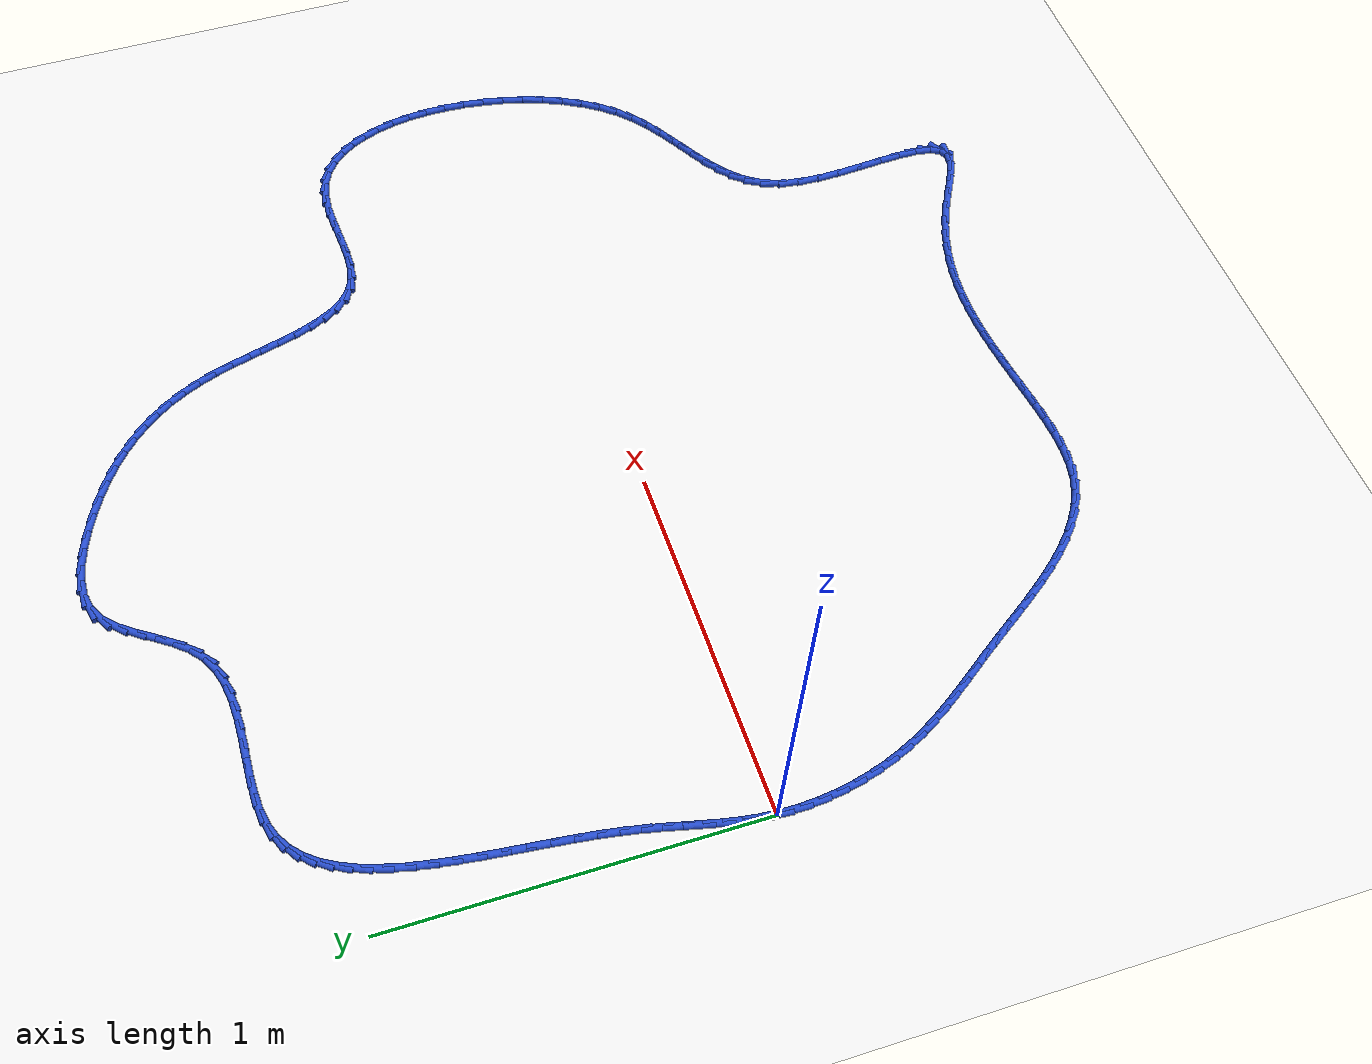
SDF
<sdf version="1.6">
 <world name="default">
  <light name="sun" type="directional">
   <pose>0 0 10 0 -0 0</pose>
   <diffuse>0.8 0.8 0.8 1</diffuse>
   <specular>0.2 0.2 0.2 1</specular>
   <attenuation>
    <range>1000</range>
    <constant>0.9</constant>
    <linear>0.01</linear>
    <quadratic>0.001</quadratic>
   </attenuation>
   <direction>-0.5 0.1 -0.9</direction>
  </light>
  <model name="ground_plane">
   <static>1</static>
   <link name="link">
    <collision name="collision">
     <geometry><plane><normal>0 0 1</normal><size>100 100</size></plane></geometry>
     <surface><friction><ode><mu>100</mu><mu2>50</mu2></ode></friction></surface>
    </collision>
    <visual name="visual">
     <cast_shadows>0</cast_shadows>
     <geometry><plane><normal>0 0 1</normal><size>100 100</size></plane></geometry>
     <material>
      <script><uri>file://media/materials/scripts/gazebo.material</uri><name>Gazebo/WhiteGlow</name></script>
     </material>
    </visual>
   </link>
  </model>
  <gravity>0 0 -9.8</gravity>
  <magnetic_field>6e-06 2.3e-05 -4.2e-05</magnetic_field>
  <atmosphere type="adiabatic"/>
  <physics name="default_physics" default="0" type="ode">
   <max_step_size>0.001</max_step_size>
   <real_time_factor>1</real_time_factor>
   <real_time_update_rate>1000</real_time_update_rate>
  </physics>
  <scene><ambient>0.4 0.4 0.4 1</ambient><background>0.7 0.7 0.7 1</background><shadows>1</shadows></scene>
  <spherical_coordinates>
   <surface_model>EARTH_WGS84</surface_model>
   <latitude_deg>0</latitude_deg>
   <longitude_deg>0</longitude_deg>
   <elevation>0</elevation>
   <heading_deg>0</heading_deg>
  </spherical_coordinates>
  <model name="line">
   <link name="link_0">
    <pose>1.734723475976807e-18 -6.938893903907228e-18 0.01 0 1.57 1.4833521786747628</pose>
    <collision name="collision">
     <geometry><cylinder><radius>0.01</radius><length>0.08</length></cylinder></geometry>
    </collision>
    <visual name="visual">
     <material>
      <script><name>Gazebo/Blue</name><uri>file://media/materials/scripts/gazebo.material</uri></script>
     </material>
     <geometry><cylinder><radius>0.01</radius><length>0.08</length></cylinder></geometry>
    </visual>
   </link>
   <link name="link_1">
    <pose>0.004138113100959546 0.04720224826261963 0.01 0 1.57 1.4253230461346753</pose>
    <collision name="collision">
     <geometry><cylinder><radius>0.01</radius><length>0.08</length></cylinder></geometry>
    </collision>
    <visual name="visual">
     <material>
      <script><name>Gazebo/Blue</name><uri>file://media/materials/scripts/gazebo.material</uri></script>
     </material>
     <geometry><cylinder><radius>0.01</radius><length>0.08</length></cylinder></geometry>
    </visual>
   </link>
   <link name="link_2">
    <pose>0.01096388504051575 0.09379192963262921 0.01 0 1.57 1.3823132232937732</pose>
    <collision name="collision">
     <geometry><cylinder><radius>0.01</radius><length>0.08</length></cylinder></geometry>
    </collision>
    <visual name="visual">
     <material>
      <script><name>Gazebo/Blue</name><uri>file://media/materials/scripts/gazebo.material</uri></script>
     </material>
     <geometry><cylinder><radius>0.01</radius><length>0.08</length></cylinder></geometry>
    </visual>
   </link>
   <link name="link_3">
    <pose>0.019821983189146835 0.1402308488769827 0.01 0 1.57 1.3552643515435585</pose>
    <collision name="collision">
     <geometry><cylinder><radius>0.01</radius><length>0.08</length></cylinder></geometry>
    </collision>
    <visual name="visual">
     <material>
      <script><name>Gazebo/Blue</name><uri>file://media/materials/scripts/gazebo.material</uri></script>
     </material>
     <geometry><cylinder><radius>0.01</radius><length>0.08</length></cylinder></geometry>
    </visual>
   </link>
   <link name="link_4">
    <pose>0.030057074917331013 0.18698081076263404 0.01 0 1.57 1.3441982621026298</pose>
    <collision name="collision">
     <geometry><cylinder><radius>0.01</radius><length>0.08</length></cylinder></geometry>
    </collision>
    <visual name="visual">
     <material>
      <script><name>Gazebo/Blue</name><uri>file://media/materials/scripts/gazebo.material</uri></script>
     </material>
     <geometry><cylinder><radius>0.01</radius><length>0.08</length></cylinder></geometry>
    </visual>
   </link>
   <link name="link_5">
    <pose>0.041013827595546525 0.23450362005653727 0.01 0 1.57 1.348454277895693</pose>
    <collision name="collision">
     <geometry><cylinder><radius>0.01</radius><length>0.08</length></cylinder></geometry>
    </collision>
    <visual name="visual">
     <material>
      <script><name>Gazebo/Blue</name><uri>file://media/materials/scripts/gazebo.material</uri></script>
     </material>
     <geometry><cylinder><radius>0.01</radius><length>0.08</length></cylinder></geometry>
    </visual>
   </link>
   <link name="link_6">
    <pose>0.05203690859427156 0.2832610815256463 0.01 0 1.57 1.3668670149796556</pose>
    <collision name="collision">
     <geometry><cylinder><radius>0.01</radius><length>0.08</length></cylinder></geometry>
    </collision>
    <visual name="visual">
     <material>
      <script><name>Gazebo/Blue</name><uri>file://media/materials/scripts/gazebo.material</uri></script>
     </material>
     <geometry><cylinder><radius>0.01</radius><length>0.08</length></cylinder></geometry>
    </visual>
   </link>
   <link name="link_7">
    <pose>0.062470985283984364 0.33371499993691517 0.01 0 1.57 1.3974777674702386</pose>
    <collision name="collision">
     <geometry><cylinder><radius>0.01</radius><length>0.08</length></cylinder></geometry>
    </collision>
    <visual name="visual">
     <material>
      <script><name>Gazebo/Blue</name><uri>file://media/materials/scripts/gazebo.material</uri></script>
     </material>
     <geometry><cylinder><radius>0.01</radius><length>0.08</length></cylinder></geometry>
    </visual>
   </link>
   <link name="link_8">
    <pose>0.07167900536336408 0.3863096790358598 0.01 0 1.57 1.4286907114682286</pose>
    <collision name="collision">
     <geometry><cylinder><radius>0.01</radius><length>0.08</length></cylinder></geometry>
    </collision>
    <visual name="visual">
     <material>
      <script><name>Gazebo/Blue</name><uri>file://media/materials/scripts/gazebo.material</uri></script>
     </material>
     <geometry><cylinder><radius>0.01</radius><length>0.08</length></cylinder></geometry>
    </visual>
   </link>
   <link name="link_9">
    <pose>0.07950735277643428 0.44102659564275165 0.01 0 1.57 1.4503571609560346</pose>
    <collision name="collision">
     <geometry><cylinder><radius>0.01</radius><length>0.08</length></cylinder></geometry>
    </collision>
    <visual name="visual">
     <material>
      <script><name>Gazebo/Blue</name><uri>file://media/materials/scripts/gazebo.material</uri></script>
     </material>
     <geometry><cylinder><radius>0.01</radius><length>0.08</length></cylinder></geometry>
    </visual>
   </link>
   <link name="link_10">
    <pose>0.08632366887201079 0.4973481908430702 0.01 0 1.57 1.4632078636833503</pose>
    <collision name="collision">
     <geometry><cylinder><radius>0.01</radius><length>0.08</length></cylinder></geometry>
    </collision>
    <visual name="visual">
     <material>
      <script><name>Gazebo/Blue</name><uri>file://media/materials/scripts/gazebo.material</uri></script>
     </material>
     <geometry><cylinder><radius>0.01</radius><length>0.08</length></cylinder></geometry>
    </visual>
   </link>
   <link name="link_11">
    <pose>0.09252145301544136 0.5547321500561655 0.01 0 1.57 1.4680106469549692</pose>
    <collision name="collision">
     <geometry><cylinder><radius>0.01</radius><length>0.08</length></cylinder></geometry>
    </collision>
    <visual name="visual">
     <material>
      <script><name>Gazebo/Blue</name><uri>file://media/materials/scripts/gazebo.material</uri></script>
     </material>
     <geometry><cylinder><radius>0.01</radius><length>0.08</length></cylinder></geometry>
    </visual>
   </link>
   <link name="link_12">
    <pose>0.09849420457207377 0.6126361587013875 0.01 0 1.57 1.4650923810912293</pose>
    <collision name="collision">
     <geometry><cylinder><radius>0.01</radius><length>0.08</length></cylinder></geometry>
    </collision>
    <visual name="visual">
     <material>
      <script><name>Gazebo/Blue</name><uri>file://media/materials/scripts/gazebo.material</uri></script>
     </material>
     <geometry><cylinder><radius>0.01</radius><length>0.08</length></cylinder></geometry>
    </visual>
   </link>
   <link name="link_13">
    <pose>0.10463542290725582 0.6705179021980868 0.01 0 1.57 1.4543761756224676</pose>
    <collision name="collision">
     <geometry><cylinder><radius>0.01</radius><length>0.08</length></cylinder></geometry>
    </collision>
    <visual name="visual">
     <material>
      <script><name>Gazebo/Blue</name><uri>file://media/materials/scripts/gazebo.material</uri></script>
     </material>
     <geometry><cylinder><radius>0.01</radius><length>0.08</length></cylinder></geometry>
    </visual>
   </link>
   <link name="link_14">
    <pose>0.11133860738633525 0.727835065965613 0.01 0 1.57 1.4353801628410665</pose>
    <collision name="collision">
     <geometry><cylinder><radius>0.01</radius><length>0.08</length></cylinder></geometry>
    </collision>
    <visual name="visual">
     <material>
      <script><name>Gazebo/Blue</name><uri>file://media/materials/scripts/gazebo.material</uri></script>
     </material>
     <geometry><cylinder><radius>0.01</radius><length>0.08</length></cylinder></geometry>
    </visual>
   </link>
   <link name="link_15">
    <pose>0.1189972573746598 0.7840453354233163 0.01 0 1.57 1.407179786286679</pose>
    <collision name="collision">
     <geometry><cylinder><radius>0.01</radius><length>0.08</length></cylinder></geometry>
    </collision>
    <visual name="visual">
     <material>
      <script><name>Gazebo/Blue</name><uri>file://media/materials/scripts/gazebo.material</uri></script>
     </material>
     <geometry><cylinder><radius>0.01</radius><length>0.08</length></cylinder></geometry>
    </visual>
   </link>
   <link name="link_16">
    <pose>0.12800487223757734 0.8386063959905475 0.01 0 1.57 1.3683352572934169</pose>
    <collision name="collision">
     <geometry><cylinder><radius>0.01</radius><length>0.08</length></cylinder></geometry>
    </collision>
    <visual name="visual">
     <material>
      <script><name>Gazebo/Blue</name><uri>file://media/materials/scripts/gazebo.material</uri></script>
     </material>
     <geometry><cylinder><radius>0.01</radius><length>0.08</length></cylinder></geometry>
    </visual>
   </link>
   <link name="link_17">
    <pose>0.13875495134043558 0.8909759330866563 0.01 0 1.57 1.3167913644758173</pose>
    <collision name="collision">
     <geometry><cylinder><radius>0.01</radius><length>0.08</length></cylinder></geometry>
    </collision>
    <visual name="visual">
     <material>
      <script><name>Gazebo/Blue</name><uri>file://media/materials/scripts/gazebo.material</uri></script>
     </material>
     <geometry><cylinder><radius>0.01</radius><length>0.08</length></cylinder></geometry>
    </visual>
   </link>
   <link name="link_18">
    <pose>0.1516409940485823 0.9406116321309927 0.01 0 1.57 1.249777381712391</pose>
    <collision name="collision">
     <geometry><cylinder><radius>0.01</radius><length>0.08</length></cylinder></geometry>
    </collision>
    <visual name="visual">
     <material>
      <script><name>Gazebo/Blue</name><uri>file://media/materials/scripts/gazebo.material</uri></script>
     </material>
     <geometry><cylinder><radius>0.01</radius><length>0.08</length></cylinder></geometry>
    </visual>
   </link>
   <link name="link_19">
    <pose>0.1670564997273652 0.9869711785429068 0.01 0 1.57 1.1637899397758265</pose>
    <collision name="collision">
     <geometry><cylinder><radius>0.01</radius><length>0.08</length></cylinder></geometry>
    </collision>
    <visual name="visual">
     <material>
      <script><name>Gazebo/Blue</name><uri>file://media/materials/scripts/gazebo.material</uri></script>
     </material>
     <geometry><cylinder><radius>0.01</radius><length>0.08</length></cylinder></geometry>
    </visual>
   </link>
   <link name="link_20">
    <pose>0.18539496774213218 1.0295122577417493 0.01 0 1.57 1.0548622389833235</pose>
    <collision name="collision">
     <geometry><cylinder><radius>0.01</radius><length>0.08</length></cylinder></geometry>
    </collision>
    <visual name="visual">
     <material>
      <script><name>Gazebo/Blue</name><uri>file://media/materials/scripts/gazebo.material</uri></script>
     </material>
     <geometry><cylinder><radius>0.01</radius><length>0.08</length></cylinder></geometry>
    </visual>
   </link>
   <link name="link_21">
    <pose>0.20704989745823102 1.06769255514687 0.01 0 1.57 0.9195136686355619</pose>
    <collision name="collision">
     <geometry><cylinder><radius>0.01</radius><length>0.08</length></cylinder></geometry>
    </collision>
    <visual name="visual">
     <material>
      <script><name>Gazebo/Blue</name><uri>file://media/materials/scripts/gazebo.material</uri></script>
     </material>
     <geometry><cylinder><radius>0.01</radius><length>0.08</length></cylinder></geometry>
    </visual>
   </link>
   <link name="link_22">
    <pose>0.23241478824100925 1.1009697561776188 0.01 0 1.57 0.756844719797566</pose>
    <collision name="collision">
     <geometry><cylinder><radius>0.01</radius><length>0.08</length></cylinder></geometry>
    </collision>
    <visual name="visual">
     <material>
      <script><name>Gazebo/Blue</name><uri>file://media/materials/scripts/gazebo.material</uri></script>
     </material>
     <geometry><cylinder><radius>0.01</radius><length>0.08</length></cylinder></geometry>
    </visual>
   </link>
   <link name="link_23">
    <pose>0.26188313945581504 1.1288015462533467 0.01 0 1.57 0.5715295678399983</pose>
    <collision name="collision">
     <geometry><cylinder><radius>0.01</radius><length>0.08</length></cylinder></geometry>
    </collision>
    <visual name="visual">
     <material>
      <script><name>Gazebo/Blue</name><uri>file://media/materials/scripts/gazebo.material</uri></script>
     </material>
     <geometry><cylinder><radius>0.01</radius><length>0.08</length></cylinder></geometry>
    </visual>
   </link>
   <link name="link_24">
    <pose>0.2958484504679959 1.1506456107934029 0.01 0 1.57 0.375515979793563</pose>
    <collision name="collision">
     <geometry><cylinder><radius>0.01</radius><length>0.08</length></cylinder></geometry>
    </collision>
    <visual name="visual">
     <material>
      <script><name>Gazebo/Blue</name><uri>file://media/materials/scripts/gazebo.material</uri></script>
     </material>
     <geometry><cylinder><radius>0.01</radius><length>0.08</length></cylinder></geometry>
    </visual>
   </link>
   <link name="link_25">
    <pose>0.33470221534080524 1.1659626439226243 0.01 0 1.57 0.20010661824349893</pose>
    <collision name="collision">
     <geometry><cylinder><radius>0.01</radius><length>0.08</length></cylinder></geometry>
    </collision>
    <visual name="visual">
     <material>
      <script><name>Gazebo/Blue</name><uri>file://media/materials/scripts/gazebo.material</uri></script>
     </material>
     <geometry><cylinder><radius>0.01</radius><length>0.08</length></cylinder></geometry>
    </visual>
   </link>
   <link name="link_26">
    <pose>0.3784246134826065 1.1748304660643687 0.01 0 1.57 0.08088205375445533</pose>
    <collision name="collision">
     <geometry><cylinder><radius>0.01</radius><length>0.08</length></cylinder></geometry>
    </collision>
    <visual name="visual">
     <material>
      <script><name>Gazebo/Blue</name><uri>file://media/materials/scripts/gazebo.material</uri></script>
     </material>
     <geometry><cylinder><radius>0.01</radius><length>0.08</length></cylinder></geometry>
    </visual>
   </link>
   <link name="link_27">
    <pose>0.4260848176880768 1.178693749352107 0.01 0 1.57 0.009631024847016514</pose>
    <collision name="collision">
     <geometry><cylinder><radius>0.01</radius><length>0.08</length></cylinder></geometry>
    </collision>
    <visual name="visual">
     <material>
      <script><name>Gazebo/Blue</name><uri>file://media/materials/scripts/gazebo.material</uri></script>
     </material>
     <geometry><cylinder><radius>0.01</radius><length>0.08</length></cylinder></geometry>
    </visual>
   </link>
   <link name="link_28">
    <pose>0.4766297659005855 1.1791805640560913 0.01 0 1.57 -0.024082108984037016</pose>
    <collision name="collision">
     <geometry><cylinder><radius>0.01</radius><length>0.08</length></cylinder></geometry>
    </collision>
    <visual name="visual">
     <material>
      <script><name>Gazebo/Blue</name><uri>file://media/materials/scripts/gazebo.material</uri></script>
     </material>
     <geometry><cylinder><radius>0.01</radius><length>0.08</length></cylinder></geometry>
    </visual>
   </link>
   <link name="link_29">
    <pose>0.5290063960635013 1.1779189804465757 0.01 0 1.57 -0.025991796539011066</pose>
    <collision name="collision">
     <geometry><cylinder><radius>0.01</radius><length>0.08</length></cylinder></geometry>
    </collision>
    <visual name="visual">
     <material>
      <script><name>Gazebo/Blue</name><uri>file://media/materials/scripts/gazebo.material</uri></script>
     </material>
     <geometry><cylinder><radius>0.01</radius><length>0.08</length></cylinder></geometry>
    </visual>
   </link>
   <link name="link_30">
    <pose>0.5821616461201928 1.176537068793814 0.01 0 1.57 0.0023795085924248655</pose>
    <collision name="collision">
     <geometry><cylinder><radius>0.01</radius><length>0.08</length></cylinder></geometry>
    </collision>
    <visual name="visual">
     <material>
      <script><name>Gazebo/Blue</name><uri>file://media/materials/scripts/gazebo.material</uri></script>
     </material>
     <geometry><cylinder><radius>0.01</radius><length>0.08</length></cylinder></geometry>
    </visual>
   </link>
   <link name="link_31">
    <pose>0.6350424540140299 1.1766628993680586 0.01 0 1.57 0.06318317934950977</pose>
    <collision name="collision">
     <geometry><cylinder><radius>0.01</radius><length>0.08</length></cylinder></geometry>
    </collision>
    <visual name="visual">
     <material>
      <script><name>Gazebo/Blue</name><uri>file://media/materials/scripts/gazebo.material</uri></script>
     </material>
     <geometry><cylinder><radius>0.01</radius><length>0.08</length></cylinder></geometry>
    </visual>
   </link>
   <link name="link_32">
    <pose>0.6865957576883807 1.1799245424395637 0.01 0 1.57 0.1617844196556809</pose>
    <collision name="collision">
     <geometry><cylinder><radius>0.01</radius><length>0.08</length></cylinder></geometry>
    </collision>
    <visual name="visual">
     <material>
      <script><name>Gazebo/Blue</name><uri>file://media/materials/scripts/gazebo.material</uri></script>
     </material>
     <geometry><cylinder><radius>0.01</radius><length>0.08</length></cylinder></geometry>
    </visual>
   </link>
   <link name="link_33">
    <pose>0.7357684950866145 1.1879500682785822 0.01 0 1.57 0.30535293684550313</pose>
    <collision name="collision">
     <geometry><cylinder><radius>0.01</radius><length>0.08</length></cylinder></geometry>
    </collision>
    <visual name="visual">
     <material>
      <script><name>Gazebo/Blue</name><uri>file://media/materials/scripts/gazebo.material</uri></script>
     </material>
     <geometry><cylinder><radius>0.01</radius><length>0.08</length></cylinder></geometry>
    </visual>
   </link>
   <link name="link_34">
    <pose>0.7815076041520999 1.2023675471553674 0.01 0 1.57 0.4981536799402887</pose>
    <collision name="collision">
     <geometry><cylinder><radius>0.01</radius><length>0.08</length></cylinder></geometry>
    </collision>
    <visual name="visual">
     <material>
      <script><name>Gazebo/Blue</name><uri>file://media/materials/scripts/gazebo.material</uri></script>
     </material>
     <geometry><cylinder><radius>0.01</radius><length>0.08</length></cylinder></geometry>
    </visual>
   </link>
   <link name="link_35">
    <pose>0.822760022828206 1.2248050493401732 0.01 0 1.57 0.7242155486025778</pose>
    <collision name="collision">
     <geometry><cylinder><radius>0.01</radius><length>0.08</length></cylinder></geometry>
    </collision>
    <visual name="visual">
     <material>
      <script><name>Gazebo/Blue</name><uri>file://media/materials/scripts/gazebo.material</uri></script>
     </material>
     <geometry><cylinder><radius>0.01</radius><length>0.08</length></cylinder></geometry>
    </visual>
   </link>
   <link name="link_36">
    <pose>0.8586592164833728 1.2565598237515534 0.01 0 1.57 0.8943701556065982</pose>
    <collision name="collision">
     <geometry><cylinder><radius>0.01</radius><length>0.08</length></cylinder></geometry>
    </collision>
    <visual name="visual">
     <material>
      <script><name>Gazebo/Blue</name><uri>file://media/materials/scripts/gazebo.material</uri></script>
     </material>
     <geometry><cylinder><radius>0.01</radius><length>0.08</length></cylinder></geometry>
    </visual>
   </link>
   <link name="link_37">
    <pose>0.8901264666788101 1.295758283870552 0.01 0 1.57 0.9782559270354504</pose>
    <collision name="collision">
     <geometry><cylinder><radius>0.01</radius><length>0.08</length></cylinder></geometry>
    </collision>
    <visual name="visual">
     <material>
      <script><name>Gazebo/Blue</name><uri>file://media/materials/scripts/gazebo.material</uri></script>
     </material>
     <geometry><cylinder><radius>0.01</radius><length>0.08</length></cylinder></geometry>
    </visual>
   </link>
   <link name="link_38">
    <pose>0.9190782250101316 1.33876182928909 0.01 0 1.57 0.9893014821292205</pose>
    <collision name="collision">
     <geometry><cylinder><radius>0.01</radius><length>0.08</length></cylinder></geometry>
    </collision>
    <visual name="visual">
     <material>
      <script><name>Gazebo/Blue</name><uri>file://media/materials/scripts/gazebo.material</uri></script>
     </material>
     <geometry><cylinder><radius>0.01</radius><length>0.08</length></cylinder></geometry>
    </visual>
   </link>
   <link name="link_39">
    <pose>0.9474416768162027 1.3819128224443675 0.01 0 1.57 0.9277518231914533</pose>
    <collision name="collision">
     <geometry><cylinder><radius>0.01</radius><length>0.08</length></cylinder></geometry>
    </collision>
    <visual name="visual">
     <material>
      <script><name>Gazebo/Blue</name><uri>file://media/materials/scripts/gazebo.material</uri></script>
     </material>
     <geometry><cylinder><radius>0.01</radius><length>0.08</length></cylinder></geometry>
    </visual>
   </link>
   <link name="link_40">
    <pose>0.9771440074358878 1.4215536257735848 0.01 0 1.57 0.7778278854162246</pose>
    <collision name="collision">
     <geometry><cylinder><radius>0.01</radius><length>0.08</length></cylinder></geometry>
    </collision>
    <visual name="visual">
     <material>
      <script><name>Gazebo/Blue</name><uri>file://media/materials/scripts/gazebo.material</uri></script>
     </material>
     <geometry><cylinder><radius>0.01</radius><length>0.08</length></cylinder></geometry>
    </visual>
   </link>
   <link name="link_41">
    <pose>1.0101124022080512 1.454026601713942 0.01 0 1.57 0.5176113235397699</pose>
    <collision name="collision">
     <geometry><cylinder><radius>0.01</radius><length>0.08</length></cylinder></geometry>
    </collision>
    <visual name="visual">
     <material>
      <script><name>Gazebo/Blue</name><uri>file://media/materials/scripts/gazebo.material</uri></script>
     </material>
     <geometry><cylinder><radius>0.01</radius><length>0.08</length></cylinder></geometry>
    </visual>
   </link>
   <link name="link_42">
    <pose>1.0482365981585824 1.4757343056589745 0.01 0 1.57 0.21765108100890893</pose>
    <collision name="collision">
     <geometry><cylinder><radius>0.01</radius><length>0.08</length></cylinder></geometry>
    </collision>
    <visual name="visual">
     <material>
      <script><name>Gazebo/Blue</name><uri>file://media/materials/scripts/gazebo.material</uri></script>
     </material>
     <geometry><cylinder><radius>0.01</radius><length>0.08</length></cylinder></geometry>
    </visual>
   </link>
   <link name="link_43">
    <pose>1.091960079651133 1.4854039430713437 0.01 0 1.57 -0.013159235292218796</pose>
    <collision name="collision">
     <geometry><cylinder><radius>0.01</radius><length>0.08</length></cylinder></geometry>
    </collision>
    <visual name="visual">
     <material>
      <script><name>Gazebo/Blue</name><uri>file://media/materials/scripts/gazebo.material</uri></script>
     </material>
     <geometry><cylinder><radius>0.01</radius><length>0.08</length></cylinder></geometry>
    </visual>
   </link>
   <link name="link_44">
    <pose>1.1398531042069149 1.4847736711114907 0.01 0 1.57 -0.17617859453486232</pose>
    <collision name="collision">
     <geometry><cylinder><radius>0.01</radius><length>0.08</length></cylinder></geometry>
    </collision>
    <visual name="visual">
     <material>
      <script><name>Gazebo/Blue</name><uri>file://media/materials/scripts/gazebo.material</uri></script>
     </material>
     <geometry><cylinder><radius>0.01</radius><length>0.08</length></cylinder></geometry>
    </visual>
   </link>
   <link name="link_45">
    <pose>1.1903612908195242 1.4757819860433883 0.01 0 1.57 -0.2904586626764423</pose>
    <collision name="collision">
     <geometry><cylinder><radius>0.01</radius><length>0.08</length></cylinder></geometry>
    </collision>
    <visual name="visual">
     <material>
      <script><name>Gazebo/Blue</name><uri>file://media/materials/scripts/gazebo.material</uri></script>
     </material>
     <geometry><cylinder><radius>0.01</radius><length>0.08</length></cylinder></geometry>
    </visual>
   </link>
   <link name="link_46">
    <pose>1.2419302584825567 1.4603673841310085 0.01 0 1.57 -0.37150984166192896</pose>
    <collision name="collision">
     <geometry><cylinder><radius>0.01</radius><length>0.08</length></cylinder></geometry>
    </collision>
    <visual name="visual">
     <material>
      <script><name>Gazebo/Blue</name><uri>file://media/materials/scripts/gazebo.material</uri></script>
     </material>
     <geometry><cylinder><radius>0.01</radius><length>0.08</length></cylinder></geometry>
    </visual>
   </link>
   <link name="link_47">
    <pose>1.2930056261896095 1.4404683616383245 0.01 0 1.57 -0.43012489655888875</pose>
    <collision name="collision">
     <geometry><cylinder><radius>0.01</radius><length>0.08</length></cylinder></geometry>
    </collision>
    <visual name="visual">
     <material>
      <script><name>Gazebo/Blue</name><uri>file://media/materials/scripts/gazebo.material</uri></script>
     </material>
     <geometry><cylinder><radius>0.01</radius><length>0.08</length></cylinder></geometry>
    </visual>
   </link>
   <link name="link_48">
    <pose>1.342085654817382 1.4179518089972698 0.01 0 1.57 -0.48375724945771054</pose>
    <collision name="collision">
     <geometry><cylinder><radius>0.01</radius><length>0.08</length></cylinder></geometry>
    </collision>
    <visual name="visual">
     <material>
      <script><name>Gazebo/Blue</name><uri>file://media/materials/scripts/gazebo.material</uri></script>
     </material>
     <geometry><cylinder><radius>0.01</radius><length>0.08</length></cylinder></geometry>
    </visual>
   </link>
   <link name="link_49">
    <pose>1.3884853993284567 1.3935735769756055 0.01 0 1.57 -0.5429903201972591</pose>
    <collision name="collision">
     <geometry><cylinder><radius>0.01</radius><length>0.08</length></cylinder></geometry>
    </collision>
    <visual name="visual">
     <material>
      <script><name>Gazebo/Blue</name><uri>file://media/materials/scripts/gazebo.material</uri></script>
     </material>
     <geometry><cylinder><radius>0.01</radius><length>0.08</length></cylinder></geometry>
    </visual>
   </link>
   <link name="link_50">
    <pose>1.432163916317122 1.3672135166626165 0.01 0 1.57 -0.6079683005864623</pose>
    <collision name="collision">
     <geometry><cylinder><radius>0.01</radius><length>0.08</length></cylinder></geometry>
    </collision>
    <visual name="visual">
     <material>
      <script><name>Gazebo/Blue</name><uri>file://media/materials/scripts/gazebo.material</uri></script>
     </material>
     <geometry><cylinder><radius>0.01</radius><length>0.08</length></cylinder></geometry>
    </visual>
   </link>
   <link name="link_51">
    <pose>1.473097732593889 1.3387277153820276 0.01 0 1.57 -0.6782926399182265</pose>
    <collision name="collision">
     <geometry><cylinder><radius>0.01</radius><length>0.08</length></cylinder></geometry>
    </collision>
    <visual name="visual">
     <material>
      <script><name>Gazebo/Blue</name><uri>file://media/materials/scripts/gazebo.material</uri></script>
     </material>
     <geometry><cylinder><radius>0.01</radius><length>0.08</length></cylinder></geometry>
    </visual>
   </link>
   <link name="link_52">
    <pose>1.5112633749692708 1.3079722604575639 0.01 0 1.57 -0.7532400528829039</pose>
    <collision name="collision">
     <geometry><cylinder><radius>0.01</radius><length>0.08</length></cylinder></geometry>
    </collision>
    <visual name="visual">
     <material>
      <script><name>Gazebo/Blue</name><uri>file://media/materials/scripts/gazebo.material</uri></script>
     </material>
     <geometry><cylinder><radius>0.01</radius><length>0.08</length></cylinder></geometry>
    </visual>
   </link>
   <link name="link_53">
    <pose>1.546637370253779 1.2748032392129511 0.01 0 1.57 -0.8317529804975258</pose>
    <collision name="collision">
     <geometry><cylinder><radius>0.01</radius><length>0.08</length></cylinder></geometry>
    </collision>
    <visual name="visual">
     <material>
      <script><name>Gazebo/Blue</name><uri>file://media/materials/scripts/gazebo.material</uri></script>
     </material>
     <geometry><cylinder><radius>0.01</radius><length>0.08</length></cylinder></geometry>
    </visual>
   </link>
   <link name="link_54">
    <pose>1.579196245257926 1.2390767389719142 0.01 0 1.57 -0.9124842013625839</pose>
    <collision name="collision">
     <geometry><cylinder><radius>0.01</radius><length>0.08</length></cylinder></geometry>
    </collision>
    <visual name="visual">
     <material>
      <script><name>Gazebo/Blue</name><uri>file://media/materials/scripts/gazebo.material</uri></script>
     </material>
     <geometry><cylinder><radius>0.01</radius><length>0.08</length></cylinder></geometry>
    </visual>
   </link>
   <link name="link_55">
    <pose>1.6089165267922243 1.2006488470581775 0.01 0 1.57 -0.9938994518358901</pose>
    <collision name="collision">
     <geometry><cylinder><radius>0.01</radius><length>0.08</length></cylinder></geometry>
    </collision>
    <visual name="visual">
     <material>
      <script><name>Gazebo/Blue</name><uri>file://media/materials/scripts/gazebo.material</uri></script>
     </material>
     <geometry><cylinder><radius>0.01</radius><length>0.08</length></cylinder></geometry>
    </visual>
   </link>
   <link name="link_56">
    <pose>1.6357747416671855 1.1593756507954671 0.01 0 1.57 -1.0744224634320925</pose>
    <collision name="collision">
     <geometry><cylinder><radius>0.01</radius><length>0.08</length></cylinder></geometry>
    </collision>
    <visual name="visual">
     <material>
      <script><name>Gazebo/Blue</name><uri>file://media/materials/scripts/gazebo.material</uri></script>
     </material>
     <geometry><cylinder><radius>0.01</radius><length>0.08</length></cylinder></geometry>
    </visual>
   </link>
   <link name="link_57">
    <pose>1.6597474166933224 1.1151132375075077 0.01 0 1.57 -1.1525900352057565</pose>
    <collision name="collision">
     <geometry><cylinder><radius>0.01</radius><length>0.08</length></cylinder></geometry>
    </collision>
    <visual name="visual">
     <material>
      <script><name>Gazebo/Blue</name><uri>file://media/materials/scripts/gazebo.material</uri></script>
     </material>
     <geometry><cylinder><radius>0.01</radius><length>0.08</length></cylinder></geometry>
    </visual>
   </link>
   <link name="link_58">
    <pose>1.6808110786811465 1.0677176945180238 0.01 0 1.57 -1.2253568373779555</pose>
    <collision name="collision">
     <geometry><cylinder><radius>0.01</radius><length>0.08</length></cylinder></geometry>
    </collision>
    <visual name="visual">
     <material>
      <script><name>Gazebo/Blue</name><uri>file://media/materials/scripts/gazebo.material</uri></script>
     </material>
     <geometry><cylinder><radius>0.01</radius><length>0.08</length></cylinder></geometry>
    </visual>
   </link>
   <link name="link_59">
    <pose>1.6990101565443534 1.0171462796611783 0.01 0 1.57 -1.277911295845203</pose>
    <collision name="collision">
     <geometry><cylinder><radius>0.01</radius><length>0.08</length></cylinder></geometry>
    </collision>
    <visual name="visual">
     <material>
      <script><name>Gazebo/Blue</name><uri>file://media/materials/scripts/gazebo.material</uri></script>
     </material>
     <geometry><cylinder><radius>0.01</radius><length>0.08</length></cylinder></geometry>
    </visual>
   </link>
   <link name="link_60">
    <pose>1.7149699516670351 0.9642217197562436 0.01 0 1.57 -1.306111012763367</pose>
    <collision name="collision">
     <geometry><cylinder><radius>0.01</radius><length>0.08</length></cylinder></geometry>
    </collision>
    <visual name="visual">
     <material>
      <script><name>Gazebo/Blue</name><uri>file://media/materials/scripts/gazebo.material</uri></script>
     </material>
     <geometry><cylinder><radius>0.01</radius><length>0.08</length></cylinder></geometry>
    </visual>
   </link>
   <link name="link_61">
    <pose>1.7296106138185892 0.9102060499832694 0.01 0 1.57 -1.3121663145126359</pose>
    <collision name="collision">
     <geometry><cylinder><radius>0.01</radius><length>0.08</length></cylinder></geometry>
    </collision>
    <visual name="visual">
     <material>
      <script><name>Gazebo/Blue</name><uri>file://media/materials/scripts/gazebo.material</uri></script>
     </material>
     <geometry><cylinder><radius>0.01</radius><length>0.08</length></cylinder></geometry>
    </visual>
   </link>
   <link name="link_62">
    <pose>1.74385460582124 0.8563647518475959 0.01 0 1.57 -1.2960652116952824</pose>
    <collision name="collision">
     <geometry><cylinder><radius>0.01</radius><length>0.08</length></cylinder></geometry>
    </collision>
    <visual name="visual">
     <material>
      <script><name>Gazebo/Blue</name><uri>file://media/materials/scripts/gazebo.material</uri></script>
     </material>
     <geometry><cylinder><radius>0.01</radius><length>0.08</length></cylinder></geometry>
    </visual>
   </link>
   <link name="link_63">
    <pose>1.7586243904972136 0.8039633068545613 0.01 0 1.57 -1.2553490747021114</pose>
    <collision name="collision">
     <geometry><cylinder><radius>0.01</radius><length>0.08</length></cylinder></geometry>
    </collision>
    <visual name="visual">
     <material>
      <script><name>Gazebo/Blue</name><uri>file://media/materials/scripts/gazebo.material</uri></script>
     </material>
     <geometry><cylinder><radius>0.01</radius><length>0.08</length></cylinder></geometry>
    </visual>
   </link>
   <link name="link_64">
    <pose>1.774842430668736 0.7542671965095069 0.01 0 1.57 -1.1846723200631302</pose>
    <collision name="collision">
     <geometry><cylinder><radius>0.01</radius><length>0.08</length></cylinder></geometry>
    </collision>
    <visual name="visual">
     <material>
      <script><name>Gazebo/Blue</name><uri>file://media/materials/scripts/gazebo.material</uri></script>
     </material>
     <geometry><cylinder><radius>0.01</radius><length>0.08</length></cylinder></geometry>
    </visual>
   </link>
   <link name="link_65">
    <pose>1.7934311891580335 0.7085419023177721 0.01 0 1.57 -1.075321195104579</pose>
    <collision name="collision">
     <geometry><cylinder><radius>0.01</radius><length>0.08</length></cylinder></geometry>
    </collision>
    <visual name="visual">
     <material>
      <script><name>Gazebo/Blue</name><uri>file://media/materials/scripts/gazebo.material</uri></script>
     </material>
     <geometry><cylinder><radius>0.01</radius><length>0.08</length></cylinder></geometry>
    </visual>
   </link>
   <link name="link_66">
    <pose>1.8153131287873314 0.6680529057846958 0.01 0 1.57 -0.9159595203525668</pose>
    <collision name="collision">
     <geometry><cylinder><radius>0.01</radius><length>0.08</length></cylinder></geometry>
    </collision>
    <visual name="visual">
     <material>
      <script><name>Gazebo/Blue</name><uri>file://media/materials/scripts/gazebo.material</uri></script>
     </material>
     <geometry><cylinder><radius>0.01</radius><length>0.08</length></cylinder></geometry>
    </visual>
   </link>
   <link name="link_67">
    <pose>1.841410712378856 0.634065688415619 0.01 0 1.57 -0.6983214270165936</pose>
    <collision name="collision">
     <geometry><cylinder><radius>0.01</radius><length>0.08</length></cylinder></geometry>
    </collision>
    <visual name="visual">
     <material>
      <script><name>Gazebo/Blue</name><uri>file://media/materials/scripts/gazebo.material</uri></script>
     </material>
     <geometry><cylinder><radius>0.01</radius><length>0.08</length></cylinder></geometry>
    </visual>
   </link>
   <link name="link_68">
    <pose>1.872646402754834 0.6078457317158806 0.01 0 1.57 -0.43341419690118843</pose>
    <collision name="collision">
     <geometry><cylinder><radius>0.01</radius><length>0.08</length></cylinder></geometry>
    </collision>
    <visual name="visual">
     <material>
      <script><name>Gazebo/Blue</name><uri>file://media/materials/scripts/gazebo.material</uri></script>
     </material>
     <geometry><cylinder><radius>0.01</radius><length>0.08</length></cylinder></geometry>
    </visual>
   </link>
   <link name="link_69">
    <pose>1.9099061513840796 0.5906034165425549 0.01 0 1.57 -0.19762858855695492</pose>
    <collision name="collision">
     <geometry><cylinder><radius>0.01</radius><length>0.08</length></cylinder></geometry>
    </collision>
    <visual name="visual">
     <material>
      <script><name>Gazebo/Blue</name><uri>file://media/materials/scripts/gazebo.material</uri></script>
     </material>
     <geometry><cylinder><radius>0.01</radius><length>0.08</length></cylinder></geometry>
    </visual>
   </link>
   <link name="link_70">
    <pose>1.9530285333860713 0.5819684889518411 0.01 0 1.57 -0.04561727477478427</pose>
    <collision name="collision">
     <geometry><cylinder><radius>0.01</radius><length>0.08</length></cylinder></geometry>
    </collision>
    <visual name="visual">
     <material>
      <script><name>Gazebo/Blue</name><uri>file://media/materials/scripts/gazebo.material</uri></script>
     </material>
     <geometry><cylinder><radius>0.01</radius><length>0.08</length></cylinder></geometry>
    </visual>
   </link>
   <link name="link_71">
    <pose>2.0006745013764835 0.5797935008586086 0.01 0 1.57 0.04021876936893844</pose>
    <collision name="collision">
     <geometry><cylinder><radius>0.01</radius><length>0.08</length></cylinder></geometry>
    </collision>
    <visual name="visual">
     <material>
      <script><name>Gazebo/Blue</name><uri>file://media/materials/scripts/gazebo.material</uri></script>
     </material>
     <geometry><cylinder><radius>0.01</radius><length>0.08</length></cylinder></geometry>
    </visual>
   </link>
   <link name="link_72">
    <pose>2.05144233515224 0.5818364222841795 0.01 0 1.57 0.07641702517180052</pose>
    <collision name="collision">
     <geometry><cylinder><radius>0.01</radius><length>0.08</length></cylinder></geometry>
    </collision>
    <visual name="visual">
     <material>
      <script><name>Gazebo/Blue</name><uri>file://media/materials/scripts/gazebo.material</uri></script>
     </material>
     <geometry><cylinder><radius>0.01</radius><length>0.08</length></cylinder></geometry>
    </visual>
   </link>
   <link name="link_73">
    <pose>2.103930314510269 0.5858552232498762 0.01 0 1.57 0.07094503947073964</pose>
    <collision name="collision">
     <geometry><cylinder><radius>0.01</radius><length>0.08</length></cylinder></geometry>
    </collision>
    <visual name="visual">
     <material>
      <script><name>Gazebo/Blue</name><uri>file://media/materials/scripts/gazebo.material</uri></script>
     </material>
     <geometry><cylinder><radius>0.01</radius><length>0.08</length></cylinder></geometry>
    </visual>
   </link>
   <link name="link_74">
    <pose>2.1567367192474984 0.5896078737770212 0.01 0 1.57 0.024055592485921002</pose>
    <collision name="collision">
     <geometry><cylinder><radius>0.01</radius><length>0.08</length></cylinder></geometry>
    </collision>
    <visual name="visual">
     <material>
      <script><name>Gazebo/Blue</name><uri>file://media/materials/scripts/gazebo.material</uri></script>
     </material>
     <geometry><cylinder><radius>0.01</radius><length>0.08</length></cylinder></geometry>
    </visual>
   </link>
   <link name="link_75">
    <pose>2.208459829160854 0.5908523438869365 0.01 0 1.57 -0.07107980603028365</pose>
    <collision name="collision">
     <geometry><cylinder><radius>0.01</radius><length>0.08</length></cylinder></geometry>
    </collision>
    <visual name="visual">
     <material>
      <script><name>Gazebo/Blue</name><uri>file://media/materials/scripts/gazebo.material</uri></script>
     </material>
     <geometry><cylinder><radius>0.01</radius><length>0.08</length></cylinder></geometry>
    </visual>
   </link>
   <link name="link_76">
    <pose>2.257697924047264 0.5873466036009447 0.01 0 1.57 -0.2271984995820998</pose>
    <collision name="collision">
     <geometry><cylinder><radius>0.01</radius><length>0.08</length></cylinder></geometry>
    </collision>
    <visual name="visual">
     <material>
      <script><name>Gazebo/Blue</name><uri>file://media/materials/scripts/gazebo.material</uri></script>
     </material>
     <geometry><cylinder><radius>0.01</radius><length>0.08</length></cylinder></geometry>
    </visual>
   </link>
   <link name="link_77">
    <pose>2.3030550958625855 0.5768604697796517 0.01 0 1.57 -0.43144308150764904</pose>
    <collision name="collision">
     <geometry><cylinder><radius>0.01</radius><length>0.08</length></cylinder></geometry>
    </collision>
    <visual name="visual">
     <material>
      <script><name>Gazebo/Blue</name><uri>file://media/materials/scripts/gazebo.material</uri></script>
     </material>
     <geometry><cylinder><radius>0.01</radius><length>0.08</length></cylinder></geometry>
    </visual>
   </link>
   <link name="link_78">
    <pose>2.3436336937689153 0.5581793497234452 0.01 0 1.57 -0.6341119963967284</pose>
    <collision name="collision">
     <geometry><cylinder><radius>0.01</radius><length>0.08</length></cylinder></geometry>
    </collision>
    <visual name="visual">
     <material>
      <script><name>Gazebo/Blue</name><uri>file://media/materials/scripts/gazebo.material</uri></script>
     </material>
     <geometry><cylinder><radius>0.01</radius><length>0.08</length></cylinder></geometry>
    </visual>
   </link>
   <link name="link_79">
    <pose>2.3794094033955324 0.5318687597921967 0.01 0 1.57 -0.8189782340382755</pose>
    <collision name="collision">
     <geometry><cylinder><radius>0.01</radius><length>0.08</length></cylinder></geometry>
    </collision>
    <visual name="visual">
     <material>
      <script><name>Gazebo/Blue</name><uri>file://media/materials/scripts/gazebo.material</uri></script>
     </material>
     <geometry><cylinder><radius>0.01</radius><length>0.08</length></cylinder></geometry>
    </visual>
   </link>
   <link name="link_80">
    <pose>2.410446227298878 0.4986742314580041 0.01 0 1.57 -0.9803338812710312</pose>
    <collision name="collision">
     <geometry><cylinder><radius>0.01</radius><length>0.08</length></cylinder></geometry>
    </collision>
    <visual name="visual">
     <material>
      <script><name>Gazebo/Blue</name><uri>file://media/materials/scripts/gazebo.material</uri></script>
     </material>
     <geometry><cylinder><radius>0.01</radius><length>0.08</length></cylinder></geometry>
    </visual>
   </link>
   <link name="link_81">
    <pose>2.4368081680353932 0.45934129619296427 0.01 0 1.57 -1.1181524190095937</pose>
    <collision name="collision">
     <geometry><cylinder><radius>0.01</radius><length>0.08</length></cylinder></geometry>
    </collision>
    <visual name="visual">
     <material>
      <script><name>Gazebo/Blue</name><uri>file://media/materials/scripts/gazebo.material</uri></script>
     </material>
     <geometry><cylinder><radius>0.01</radius><length>0.08</length></cylinder></geometry>
    </visual>
   </link>
   <link name="link_82">
    <pose>2.4585592281615214 0.4146154854691745 0.01 0 1.57 -1.2355011004110177</pose>
    <collision name="collision">
     <geometry><cylinder><radius>0.01</radius><length>0.08</length></cylinder></geometry>
    </collision>
    <visual name="visual">
     <material>
      <script><name>Gazebo/Blue</name><uri>file://media/materials/scripts/gazebo.material</uri></script>
     </material>
     <geometry><cylinder><radius>0.01</radius><length>0.08</length></cylinder></geometry>
    </visual>
   </link>
   <link name="link_83">
    <pose>2.4757634102337027 0.3652423307587322 0.01 0 1.57 -1.336399717010261</pose>
    <collision name="collision">
     <geometry><cylinder><radius>0.01</radius><length>0.08</length></cylinder></geometry>
    </collision>
    <visual name="visual">
     <material>
      <script><name>Gazebo/Blue</name><uri>file://media/materials/scripts/gazebo.material</uri></script>
     </material>
     <geometry><cylinder><radius>0.01</radius><length>0.08</length></cylinder></geometry>
    </visual>
   </link>
   <link name="link_84">
    <pose>2.48848471680838 0.311967363533734 0.01 0 1.57 -1.424719532891398</pose>
    <collision name="collision">
     <geometry><cylinder><radius>0.01</radius><length>0.08</length></cylinder></geometry>
    </collision>
    <visual name="visual">
     <material>
      <script><name>Gazebo/Blue</name><uri>file://media/materials/scripts/gazebo.material</uri></script>
     </material>
     <geometry><cylinder><radius>0.01</radius><length>0.08</length></cylinder></geometry>
    </visual>
   </link>
   <link name="link_85">
    <pose>2.4967871504419925 0.2555361152662783 0.01 0 1.57 -1.503809191341532</pose>
    <collision name="collision">
     <geometry><cylinder><radius>0.01</radius><length>0.08</length></cylinder></geometry>
    </collision>
    <visual name="visual">
     <material>
      <script><name>Gazebo/Blue</name><uri>file://media/materials/scripts/gazebo.material</uri></script>
     </material>
     <geometry><cylinder><radius>0.01</radius><length>0.08</length></cylinder></geometry>
    </visual>
   </link>
   <link name="link_86">
    <pose>2.5007347136909863 0.19669411742846182 0.01 0 1.57 1.5651226085435006</pose>
    <collision name="collision">
     <geometry><cylinder><radius>0.01</radius><length>0.08</length></cylinder></geometry>
    </collision>
    <visual name="visual">
     <material>
      <script><name>Gazebo/Blue</name><uri>file://media/materials/scripts/gazebo.material</uri></script>
     </material>
     <geometry><cylinder><radius>0.01</radius><length>0.08</length></cylinder></geometry>
    </visual>
   </link>
   <link name="link_87">
    <pose>2.500391409111799 0.13618690149238163 0.01 0 1.57 1.4965330152106084</pose>
    <collision name="collision">
     <geometry><cylinder><radius>0.01</radius><length>0.08</length></cylinder></geometry>
    </collision>
    <visual name="visual">
     <material>
      <script><name>Gazebo/Blue</name><uri>file://media/materials/scripts/gazebo.material</uri></script>
     </material>
     <geometry><cylinder><radius>0.01</radius><length>0.08</length></cylinder></geometry>
    </visual>
   </link>
   <link name="link_88">
    <pose>2.495821239260874 0.07475999893013513 0.01 0 1.57 1.4299672112458717</pose>
    <collision name="collision">
     <geometry><cylinder><radius>0.01</radius><length>0.08</length></cylinder></geometry>
    </collision>
    <visual name="visual">
     <material>
      <script><name>Gazebo/Blue</name><uri>file://media/materials/scripts/gazebo.material</uri></script>
     </material>
     <geometry><cylinder><radius>0.01</radius><length>0.08</length></cylinder></geometry>
    </visual>
   </link>
   <link name="link_89">
    <pose>2.4870882066946534 0.013158941213818366 0.01 0 1.57 1.3635583925396904</pose>
    <collision name="collision">
     <geometry><cylinder><radius>0.01</radius><length>0.08</length></cylinder></geometry>
    </collision>
    <visual name="visual">
     <material>
      <script><name>Gazebo/Blue</name><uri>file://media/materials/scripts/gazebo.material</uri></script>
     </material>
     <geometry><cylinder><radius>0.01</radius><length>0.08</length></cylinder></geometry>
    </visual>
   </link>
   <link name="link_90">
    <pose>2.4742563139695792 -0.04787074018446901 0.01 0 1.57 1.2955035792887912</pose>
    <collision name="collision">
     <geometry><cylinder><radius>0.01</radius><length>0.08</length></cylinder></geometry>
    </collision>
    <visual name="visual">
     <material>
      <script><name>Gazebo/Blue</name><uri>file://media/materials/scripts/gazebo.material</uri></script>
     </material>
     <geometry><cylinder><radius>0.01</radius><length>0.08</length></cylinder></geometry>
    </visual>
   </link>
   <link name="link_91">
    <pose>2.457389563642091 -0.10758351379263104 0.01 0 1.57 1.2239593561271442</pose>
    <collision name="collision">
     <geometry><cylinder><radius>0.01</radius><length>0.08</length></cylinder></geometry>
    </collision>
    <visual name="visual">
     <material>
      <script><name>Gazebo/Blue</name><uri>file://media/materials/scripts/gazebo.material</uri></script>
     </material>
     <geometry><cylinder><radius>0.01</radius><length>0.08</length></cylinder></geometry>
    </visual>
   </link>
   <link name="link_92">
    <pose>2.4365519582686326 -0.1652338481385704 0.01 0 1.57 1.1469512393487458</pose>
    <collision name="collision">
     <geometry><cylinder><radius>0.01</radius><length>0.08</length></cylinder></geometry>
    </collision>
    <visual name="visual">
     <material>
      <script><name>Gazebo/Blue</name><uri>file://media/materials/scripts/gazebo.material</uri></script>
     </material>
     <geometry><cylinder><radius>0.01</radius><length>0.08</length></cylinder></geometry>
    </visual>
   </link>
   <link name="link_93">
    <pose>2.411807500405645 -0.22007621175018988 0.01 0 1.57 1.0623059082910338</pose>
    <collision name="collision">
     <geometry><cylinder><radius>0.01</radius><length>0.08</length></cylinder></geometry>
    </collision>
    <visual name="visual">
     <material>
      <script><name>Gazebo/Blue</name><uri>file://media/materials/scripts/gazebo.material</uri></script>
     </material>
     <geometry><cylinder><radius>0.01</radius><length>0.08</length></cylinder></geometry>
    </visual>
   </link>
   <link name="link_94">
    <pose>2.383220192609569 -0.271365073155393 0.01 0 1.57 0.9676330819131115</pose>
    <collision name="collision">
     <geometry><cylinder><radius>0.01</radius><length>0.08</length></cylinder></geometry>
    </collision>
    <visual name="visual">
     <material>
      <script><name>Gazebo/Blue</name><uri>file://media/materials/scripts/gazebo.material</uri></script>
     </material>
     <geometry><cylinder><radius>0.01</radius><length>0.08</length></cylinder></geometry>
    </visual>
   </link>
   <link name="link_95">
    <pose>2.350854037436848 -0.31835490088208074 0.01 0 1.57 0.860414689295662</pose>
    <collision name="collision">
     <geometry><cylinder><radius>0.01</radius><length>0.08</length></cylinder></geometry>
    </collision>
    <visual name="visual">
     <material>
      <script><name>Gazebo/Blue</name><uri>file://media/materials/scripts/gazebo.material</uri></script>
     </material>
     <geometry><cylinder><radius>0.01</radius><length>0.08</length></cylinder></geometry>
    </visual>
   </link>
   <link name="link_96">
    <pose>2.314773037792205 -0.36030016417041155 0.01 0 1.57 0.744965603380325</pose>
    <collision name="collision">
     <geometry><cylinder><radius>0.01</radius><length>0.08</length></cylinder></geometry>
    </collision>
    <visual name="visual">
     <material>
      <script><name>Gazebo/Blue</name><uri>file://media/materials/scripts/gazebo.material</uri></script>
     </material>
     <geometry><cylinder><radius>0.01</radius><length>0.08</length></cylinder></geometry>
    </visual>
   </link>
   <link name="link_97">
    <pose>2.2752053171679005 -0.3967909670873308 0.01 0 1.57 0.6476040961380963</pose>
    <collision name="collision">
     <geometry><cylinder><radius>0.01</radius><length>0.08</length></cylinder></geometry>
    </collision>
    <visual name="visual">
     <material>
      <script><name>Gazebo/Blue</name><uri>file://media/materials/scripts/gazebo.material</uri></script>
     </material>
     <geometry><cylinder><radius>0.01</radius><length>0.08</length></cylinder></geometry>
    </visual>
   </link>
   <link name="link_98">
    <pose>2.233010342654311 -0.42870854299915423 0.01 0 1.57 0.5773192533011722</pose>
    <collision name="collision">
     <geometry><cylinder><radius>0.01</radius><length>0.08</length></cylinder></geometry>
    </collision>
    <visual name="visual">
     <material>
      <script><name>Gazebo/Blue</name><uri>file://media/materials/scripts/gazebo.material</uri></script>
     </material>
     <geometry><cylinder><radius>0.01</radius><length>0.08</length></cylinder></geometry>
    </visual>
   </link>
   <link name="link_99">
    <pose>2.1891993714259845 -0.45724454360163796 0.01 0 1.57 0.5353824694238893</pose>
    <collision name="collision">
     <geometry><cylinder><radius>0.01</radius><length>0.08</length></cylinder></geometry>
    </collision>
    <visual name="visual">
     <material>
      <script><name>Gazebo/Blue</name><uri>file://media/materials/scripts/gazebo.material</uri></script>
     </material>
     <geometry><cylinder><radius>0.01</radius><length>0.08</length></cylinder></geometry>
    </visual>
   </link>
   <link name="link_100">
    <pose>2.1447836606574744 -0.48359062059053615 0.01 0 1.57 0.522560056136733</pose>
    <collision name="collision">
     <geometry><cylinder><radius>0.01</radius><length>0.08</length></cylinder></geometry>
    </collision>
    <visual name="visual">
     <material>
      <script><name>Gazebo/Blue</name><uri>file://media/materials/scripts/gazebo.material</uri></script>
     </material>
     <geometry><cylinder><radius>0.01</radius><length>0.08</length></cylinder></geometry>
    </visual>
   </link>
   <link name="link_101">
    <pose>2.100774467523328 -0.5089384256616047 0.01 0 1.57 0.5401835358497639</pose>
    <collision name="collision">
     <geometry><cylinder><radius>0.01</radius><length>0.08</length></cylinder></geometry>
    </collision>
    <visual name="visual">
     <material>
      <script><name>Gazebo/Blue</name><uri>file://media/materials/scripts/gazebo.material</uri></script>
     </material>
     <geometry><cylinder><radius>0.01</radius><length>0.08</length></cylinder></geometry>
    </visual>
   </link>
   <link name="link_102">
    <pose>2.058183049198096 -0.5344796105105993 0.01 0 1.57 0.5906060010589071</pose>
    <collision name="collision">
     <geometry><cylinder><radius>0.01</radius><length>0.08</length></cylinder></geometry>
    </collision>
    <visual name="visual">
     <material>
      <script><name>Gazebo/Blue</name><uri>file://media/materials/scripts/gazebo.material</uri></script>
     </material>
     <geometry><cylinder><radius>0.01</radius><length>0.08</length></cylinder></geometry>
    </visual>
   </link>
   <link name="link_103">
    <pose>2.0180206628563284 -0.5614058268332753 0.01 0 1.57 0.6768167445593142</pose>
    <collision name="collision">
     <geometry><cylinder><radius>0.01</radius><length>0.08</length></cylinder></geometry>
    </collision>
    <visual name="visual">
     <material>
      <script><name>Gazebo/Blue</name><uri>file://media/materials/scripts/gazebo.material</uri></script>
     </material>
     <geometry><cylinder><radius>0.01</radius><length>0.08</length></cylinder></geometry>
    </visual>
   </link>
   <link name="link_104">
    <pose>1.9812985656725728 -0.5909087263253883 0.01 0 1.57 0.8006648479722944</pose>
    <collision name="collision">
     <geometry><cylinder><radius>0.01</radius><length>0.08</length></cylinder></geometry>
    </collision>
    <visual name="visual">
     <material>
      <script><name>Gazebo/Blue</name><uri>file://media/materials/scripts/gazebo.material</uri></script>
     </material>
     <geometry><cylinder><radius>0.01</radius><length>0.08</length></cylinder></geometry>
    </visual>
   </link>
   <link name="link_105">
    <pose>1.9490280148213814 -0.6241799606826927 0.01 0 1.57 0.9592651800630944</pose>
    <collision name="collision">
     <geometry><cylinder><radius>0.01</radius><length>0.08</length></cylinder></geometry>
    </collision>
    <visual name="visual">
     <material>
      <script><name>Gazebo/Blue</name><uri>file://media/materials/scripts/gazebo.material</uri></script>
     </material>
     <geometry><cylinder><radius>0.01</radius><length>0.08</length></cylinder></geometry>
    </visual>
   </link>
   <link name="link_106">
    <pose>1.922220267477304 -0.6624111816009446 0.01 0 1.57 1.1411915288482528</pose>
    <collision name="collision">
     <geometry><cylinder><radius>0.01</radius><length>0.08</length></cylinder></geometry>
    </collision>
    <visual name="visual">
     <material>
      <script><name>Gazebo/Blue</name><uri>file://media/materials/scripts/gazebo.material</uri></script>
     </material>
     <geometry><cylinder><radius>0.01</radius><length>0.08</length></cylinder></geometry>
    </visual>
   </link>
   <link name="link_107">
    <pose>1.9018865808148897 -0.7067940407758996 0.01 0 1.57 1.3251898674702867</pose>
    <collision name="collision">
     <geometry><cylinder><radius>0.01</radius><length>0.08</length></cylinder></geometry>
    </collision>
    <visual name="visual">
     <material>
      <script><name>Gazebo/Blue</name><uri>file://media/materials/scripts/gazebo.material</uri></script>
     </material>
     <geometry><cylinder><radius>0.01</radius><length>0.08</length></cylinder></geometry>
    </visual>
   </link>
   <link name="link_108">
    <pose>1.8889490783106362 -0.7584063206875965 0.01 0 1.57 1.4667762088494005</pose>
    <collision name="collision">
     <geometry><cylinder><radius>0.01</radius><length>0.08</length></cylinder></geometry>
    </collision>
    <visual name="visual">
     <material>
      <script><name>Gazebo/Blue</name><uri>file://media/materials/scripts/gazebo.material</uri></script>
     </material>
     <geometry><cylinder><radius>0.01</radius><length>0.08</length></cylinder></geometry>
    </visual>
   </link>
   <link name="link_109">
    <pose>1.8828862089376857 -0.8164814947944673 0.01 0 1.57 1.5566634035106777</pose>
    <collision name="collision">
     <geometry><cylinder><radius>0.01</radius><length>0.08</length></cylinder></geometry>
    </collision>
    <visual name="visual">
     <material>
      <script><name>Gazebo/Blue</name><uri>file://media/materials/scripts/gazebo.material</uri></script>
     </material>
     <geometry><cylinder><radius>0.01</radius><length>0.08</length></cylinder></geometry>
    </visual>
   </link>
   <link name="link_110">
    <pose>1.8820060038661153 -0.8787578157775285 0.01 0 1.57 -1.5306642677155144</pose>
    <collision name="collision">
     <geometry><cylinder><radius>0.01</radius><length>0.08</length></cylinder></geometry>
    </collision>
    <visual name="visual">
     <material>
      <script><name>Gazebo/Blue</name><uri>file://media/materials/scripts/gazebo.material</uri></script>
     </material>
     <geometry><cylinder><radius>0.01</radius><length>0.08</length></cylinder></geometry>
    </visual>
   </link>
   <link name="link_111">
    <pose>1.8845827673173952 -0.9429304497941744 0.01 0 1.57 -1.5033367636868913</pose>
    <collision name="collision">
     <geometry><cylinder><radius>0.01</radius><length>0.08</length></cylinder></geometry>
    </collision>
    <visual name="visual">
     <material>
      <script><name>Gazebo/Blue</name><uri>file://media/materials/scripts/gazebo.material</uri></script>
     </material>
     <geometry><cylinder><radius>0.01</radius><length>0.08</length></cylinder></geometry>
    </visual>
   </link>
   <link name="link_112">
    <pose>1.8888908035129959 -1.0066945630018034 0.01 0 1.57 -1.500257378357856</pose>
    <collision name="collision">
     <geometry><cylinder><radius>0.01</radius><length>0.08</length></cylinder></geometry>
    </collision>
    <visual name="visual">
     <material>
      <script><name>Gazebo/Blue</name><uri>file://media/materials/scripts/gazebo.material</uri></script>
     </material>
     <geometry><cylinder><radius>0.01</radius><length>0.08</length></cylinder></geometry>
    </visual>
   </link>
   <link name="link_113">
    <pose>1.893204416674387 -1.067745321557812 0.01 0 1.57 -1.5245438584699584</pose>
    <collision name="collision">
     <geometry><cylinder><radius>0.01</radius><length>0.08</length></cylinder></geometry>
    </collision>
    <visual name="visual">
     <material>
      <script><name>Gazebo/Blue</name><uri>file://media/materials/scripts/gazebo.material</uri></script>
     </material>
     <geometry><cylinder><radius>0.01</radius><length>0.08</length></cylinder></geometry>
    </visual>
   </link>
   <link name="link_114">
    <pose>1.8957979110230399 -1.1237778916195977 0.01 0 1.57 1.5533001004804743</pose>
    <collision name="collision">
     <geometry><cylinder><radius>0.01</radius><length>0.08</length></cylinder></geometry>
    </collision>
    <visual name="visual">
     <material>
      <script><name>Gazebo/Blue</name><uri>file://media/materials/scripts/gazebo.material</uri></script>
     </material>
     <geometry><cylinder><radius>0.01</radius><length>0.08</length></cylinder></geometry>
    </visual>
   </link>
   <link name="link_115">
    <pose>1.894945590780425 -1.1724874393445588 0.01 0 1.57 1.4178654907097394</pose>
    <collision name="collision">
     <geometry><cylinder><radius>0.01</radius><length>0.08</length></cylinder></geometry>
    </collision>
    <visual name="visual">
     <material>
      <script><name>Gazebo/Blue</name><uri>file://media/materials/scripts/gazebo.material</uri></script>
     </material>
     <geometry><cylinder><radius>0.01</radius><length>0.08</length></cylinder></geometry>
    </visual>
   </link>
   <link name="link_116">
    <pose>1.8889217601680124 -1.21156913089009 0.01 0 1.57 1.1265890930205877</pose>
    <collision name="collision">
     <geometry><cylinder><radius>0.01</radius><length>0.08</length></cylinder></geometry>
    </collision>
    <visual name="visual">
     <material>
      <script><name>Gazebo/Blue</name><uri>file://media/materials/scripts/gazebo.material</uri></script>
     </material>
     <geometry><cylinder><radius>0.01</radius><length>0.08</length></cylinder></geometry>
    </visual>
   </link>
   <link name="link_117">
    <pose>1.8760007234072726 -1.2387181324135894 0.01 0 1.57 0.5399113018068107</pose>
    <collision name="collision">
     <geometry><cylinder><radius>0.01</radius><length>0.08</length></cylinder></geometry>
    </collision>
    <visual name="visual">
     <material>
      <script><name>Gazebo/Blue</name><uri>file://media/materials/scripts/gazebo.material</uri></script>
     </material>
     <geometry><cylinder><radius>0.01</radius><length>0.08</length></cylinder></geometry>
    </visual>
   </link>
   <link name="link_118">
    <pose>1.8544567847196765 -1.2516296100724542 0.01 0 1.57 -0.09654531863326281</pose>
    <collision name="collision">
     <geometry><cylinder><radius>0.01</radius><length>0.08</length></cylinder></geometry>
    </collision>
    <visual name="visual">
     <material>
      <script><name>Gazebo/Blue</name><uri>file://media/materials/scripts/gazebo.material</uri></script>
     </material>
     <geometry><cylinder><radius>0.01</radius><length>0.08</length></cylinder></geometry>
    </visual>
   </link>
   <link name="link_119">
    <pose>1.8229115577545232 -1.2485745681664422 0.01 0 1.57 -0.3848978425719063</pose>
    <collision name="collision">
     <geometry><cylinder><radius>0.01</radius><length>0.08</length></cylinder></geometry>
    </collision>
    <visual name="visual">
     <material>
      <script><name>Gazebo/Blue</name><uri>file://media/materials/scripts/gazebo.material</uri></script>
     </material>
     <geometry><cylinder><radius>0.01</radius><length>0.08</length></cylinder></geometry>
    </visual>
   </link>
   <link name="link_120">
    <pose>1.7826696809703224 -1.232272459261457 0.01 0 1.57 -0.4902870545709526</pose>
    <collision name="collision">
     <geometry><cylinder><radius>0.01</radius><length>0.08</length></cylinder></geometry>
    </collision>
    <visual name="visual">
     <material>
      <script><name>Gazebo/Blue</name><uri>file://media/materials/scripts/gazebo.material</uri></script>
     </material>
     <geometry><cylinder><radius>0.01</radius><length>0.08</length></cylinder></geometry>
    </visual>
   </link>
   <link name="link_121">
    <pose>1.73628535253424 -1.2075145027219547 0.01 0 1.57 -0.5170199239435117</pose>
    <collision name="collision">
     <geometry><cylinder><radius>0.01</radius><length>0.08</length></cylinder></geometry>
    </collision>
    <visual name="visual">
     <material>
      <script><name>Gazebo/Blue</name><uri>file://media/materials/scripts/gazebo.material</uri></script>
     </material>
     <geometry><cylinder><radius>0.01</radius><length>0.08</length></cylinder></geometry>
    </visual>
   </link>
   <link name="link_122">
    <pose>1.6863197455360506 -1.1791034823162247 0.01 0 1.57 -0.4911693146768078</pose>
    <collision name="collision">
     <geometry><cylinder><radius>0.01</radius><length>0.08</length></cylinder></geometry>
    </collision>
    <visual name="visual">
     <material>
      <script><name>Gazebo/Blue</name><uri>file://media/materials/scripts/gazebo.material</uri></script>
     </material>
     <geometry><cylinder><radius>0.01</radius><length>0.08</length></cylinder></geometry>
    </visual>
   </link>
   <link name="link_123">
    <pose>1.6353264422524296 -1.1518276196169273 0.01 0 1.57 -0.4286232499107913</pose>
    <collision name="collision">
     <geometry><cylinder><radius>0.01</radius><length>0.08</length></cylinder></geometry>
    </collision>
    <visual name="visual">
     <material>
      <script><name>Gazebo/Blue</name><uri>file://media/materials/scripts/gazebo.material</uri></script>
     </material>
     <geometry><cylinder><radius>0.01</radius><length>0.08</length></cylinder></geometry>
    </visual>
   </link>
   <link name="link_124">
    <pose>1.585002379552402 -1.1288317499286482 0.01 0 1.57 -0.3606228047868257</pose>
    <collision name="collision">
     <geometry><cylinder><radius>0.01</radius><length>0.08</length></cylinder></geometry>
    </collision>
    <visual name="visual">
     <material>
      <script><name>Gazebo/Blue</name><uri>file://media/materials/scripts/gazebo.material</uri></script>
     </material>
     <geometry><cylinder><radius>0.01</radius><length>0.08</length></cylinder></geometry>
    </visual>
   </link>
   <link name="link_125">
    <pose>1.5354130281340355 -1.1101309081995663 0.01 0 1.57 -0.2923974377686825</pose>
    <collision name="collision">
     <geometry><cylinder><radius>0.01</radius><length>0.08</length></cylinder></geometry>
    </collision>
    <visual name="visual">
     <material>
      <script><name>Gazebo/Blue</name><uri>file://media/materials/scripts/gazebo.material</uri></script>
     </material>
     <geometry><cylinder><radius>0.01</radius><length>0.08</length></cylinder></geometry>
    </visual>
   </link>
   <link name="link_126">
    <pose>1.486440839708487 -1.0953890262409018 0.01 0 1.57 -0.2254863458691191</pose>
    <collision name="collision">
     <geometry><cylinder><radius>0.01</radius><length>0.08</length></cylinder></geometry>
    </collision>
    <visual name="visual">
     <material>
      <script><name>Gazebo/Blue</name><uri>file://media/materials/scripts/gazebo.material</uri></script>
     </material>
     <geometry><cylinder><radius>0.01</radius><length>0.08</length></cylinder></geometry>
    </visual>
   </link>
   <link name="link_127">
    <pose>1.4379682659869157 -1.0842700358638766 0.01 0 1.57 -0.16144559988067128</pose>
    <collision name="collision">
     <geometry><cylinder><radius>0.01</radius><length>0.08</length></cylinder></geometry>
    </collision>
    <visual name="visual">
     <material>
      <script><name>Gazebo/Blue</name><uri>file://media/materials/scripts/gazebo.material</uri></script>
     </material>
     <geometry><cylinder><radius>0.01</radius><length>0.08</length></cylinder></geometry>
    </visual>
   </link>
   <link name="link_128">
    <pose>1.3898777586804774 -1.0764378688797105 0.01 0 1.57 -0.10171386625293406</pose>
    <collision name="collision">
     <geometry><cylinder><radius>0.01</radius><length>0.08</length></cylinder></geometry>
    </collision>
    <visual name="visual">
     <material>
      <script><name>Gazebo/Blue</name><uri>file://media/materials/scripts/gazebo.material</uri></script>
     </material>
     <geometry><cylinder><radius>0.01</radius><length>0.08</length></cylinder></geometry>
    </visual>
   </link>
   <link name="link_129">
    <pose>1.3420517695003291 -1.0715564570996243 0.01 0 1.57 -0.04750557736145469</pose>
    <collision name="collision">
     <geometry><cylinder><radius>0.01</radius><length>0.08</length></cylinder></geometry>
    </collision>
    <visual name="visual">
     <material>
      <script><name>Gazebo/Blue</name><uri>file://media/materials/scripts/gazebo.material</uri></script>
     </material>
     <geometry><cylinder><radius>0.01</radius><length>0.08</length></cylinder></geometry>
    </visual>
   </link>
   <link name="link_130">
    <pose>1.2943727501576294 -1.0692897323348394 0.01 0 1.57 0.0002496151497739468</pose>
    <collision name="collision">
     <geometry><cylinder><radius>0.01</radius><length>0.08</length></cylinder></geometry>
    </collision>
    <visual name="visual">
     <material>
      <script><name>Gazebo/Blue</name><uri>file://media/materials/scripts/gazebo.material</uri></script>
     </material>
     <geometry><cylinder><radius>0.01</radius><length>0.08</length></cylinder></geometry>
    </visual>
   </link>
   <link name="link_131">
    <pose>1.2467231523635336 -1.0693016263965764 0.01 0 1.57 0.040918451985925544</pose>
    <collision name="collision">
     <geometry><cylinder><radius>0.01</radius><length>0.08</length></cylinder></geometry>
    </collision>
    <visual name="visual">
     <material>
      <script><name>Gazebo/Blue</name><uri>file://media/materials/scripts/gazebo.material</uri></script>
     </material>
     <geometry><cylinder><radius>0.01</radius><length>0.08</length></cylinder></geometry>
    </visual>
   </link>
   <link name="link_132">
    <pose>1.198985427829201 -1.071256071096056 0.01 0 1.57 0.07413743589017092</pose>
    <collision name="collision">
     <geometry><cylinder><radius>0.01</radius><length>0.08</length></cylinder></geometry>
    </collision>
    <visual name="visual">
     <material>
      <script><name>Gazebo/Blue</name><uri>file://media/materials/scripts/gazebo.material</uri></script>
     </material>
     <geometry><cylinder><radius>0.01</radius><length>0.08</length></cylinder></geometry>
    </visual>
   </link>
   <link name="link_133">
    <pose>1.1510420282657878 -1.0748169982444993 0.01 0 1.57 0.0997646349281113</pose>
    <collision name="collision">
     <geometry><cylinder><radius>0.01</radius><length>0.08</length></cylinder></geometry>
    </collision>
    <visual name="visual">
     <material>
      <script><name>Gazebo/Blue</name><uri>file://media/materials/scripts/gazebo.material</uri></script>
     </material>
     <geometry><cylinder><radius>0.01</radius><length>0.08</length></cylinder></geometry>
    </visual>
   </link>
   <link name="link_134">
    <pose>1.102775405384452 -1.079648339653127 0.01 0 1.57 0.11782566792402432</pose>
    <collision name="collision">
     <geometry><cylinder><radius>0.01</radius><length>0.08</length></cylinder></geometry>
    </collision>
    <visual name="visual">
     <material>
      <script><name>Gazebo/Blue</name><uri>file://media/materials/scripts/gazebo.material</uri></script>
     </material>
     <geometry><cylinder><radius>0.01</radius><length>0.08</length></cylinder></geometry>
    </visual>
   </link>
   <link name="link_135">
    <pose>1.0540680108963498 -1.0854140271331592 0.01 0 1.57 0.1284649612448785</pose>
    <collision name="collision">
     <geometry><cylinder><radius>0.01</radius><length>0.08</length></cylinder></geometry>
    </collision>
    <visual name="visual">
     <material>
      <script><name>Gazebo/Blue</name><uri>file://media/materials/scripts/gazebo.material</uri></script>
     </material>
     <geometry><cylinder><radius>0.01</radius><length>0.08</length></cylinder></geometry>
    </visual>
   </link>
   <link name="link_136">
    <pose>1.004802296512638 -1.0917779924958178 0.01 0 1.57 0.13180124155252315</pose>
    <collision name="collision">
     <geometry><cylinder><radius>0.01</radius><length>0.08</length></cylinder></geometry>
    </collision>
    <visual name="visual">
     <material>
      <script><name>Gazebo/Blue</name><uri>file://media/materials/scripts/gazebo.material</uri></script>
     </material>
     <geometry><cylinder><radius>0.01</radius><length>0.08</length></cylinder></geometry>
    </visual>
   </link>
   <link name="link_137">
    <pose>0.954866906038727 -1.0983979162415713 0.01 0 1.57 0.12360386644532671</pose>
    <collision name="collision">
     <geometry><cylinder><radius>0.01</radius><length>0.08</length></cylinder></geometry>
    </collision>
    <visual name="visual">
     <material>
      <script><name>Gazebo/Blue</name><uri>file://media/materials/scripts/gazebo.material</uri></script>
     </material>
     <geometry><cylinder><radius>0.01</radius><length>0.08</length></cylinder></geometry>
    </visual>
   </link>
   <link name="link_138">
    <pose>0.904413319689962 -1.104666128892571 0.01 0 1.57 0.09778638870078506</pose>
    <collision name="collision">
     <geometry><cylinder><radius>0.01</radius><length>0.08</length></cylinder></geometry>
    </collision>
    <visual name="visual">
     <material>
      <script><name>Gazebo/Blue</name><uri>file://media/materials/scripts/gazebo.material</uri></script>
     </material>
     <geometry><cylinder><radius>0.01</radius><length>0.08</length></cylinder></geometry>
    </visual>
   </link>
   <link name="link_139">
    <pose>0.8539478288487486 -1.1096167566585995 0.01 0 1.57 0.05284430850764454</pose>
    <collision name="collision">
     <geometry><cylinder><radius>0.01</radius><length>0.08</length></cylinder></geometry>
    </collision>
    <visual name="visual">
     <material>
      <script><name>Gazebo/Blue</name><uri>file://media/materials/scripts/gazebo.material</uri></script>
     </material>
     <geometry><cylinder><radius>0.01</radius><length>0.08</length></cylinder></geometry>
    </visual>
   </link>
   <link name="link_140">
    <pose>0.8040018326744004 -1.1122585778607657 0.01 0 1.57 -0.013460801885786704</pose>
    <collision name="collision">
     <geometry><cylinder><radius>0.01</radius><length>0.08</length></cylinder></geometry>
    </collision>
    <visual name="visual">
     <material>
      <script><name>Gazebo/Blue</name><uri>file://media/materials/scripts/gazebo.material</uri></script>
     </material>
     <geometry><cylinder><radius>0.01</radius><length>0.08</length></cylinder></geometry>
    </visual>
   </link>
   <link name="link_141">
    <pose>0.7551067303262327 -1.111600370820181 0.01 0 1.57 -0.1042322324185465</pose>
    <collision name="collision">
     <geometry><cylinder><radius>0.01</radius><length>0.08</length></cylinder></geometry>
    </collision>
    <visual name="visual">
     <material>
      <script><name>Gazebo/Blue</name><uri>file://media/materials/scripts/gazebo.material</uri></script>
     </material>
     <geometry><cylinder><radius>0.01</radius><length>0.08</length></cylinder></geometry>
    </visual>
   </link>
   <link name="link_142">
    <pose>0.7077939209635588 -1.1066509138579543 0.01 0 1.57 -0.22262231547972017</pose>
    <collision name="collision">
     <geometry><cylinder><radius>0.01</radius><length>0.08</length></cylinder></geometry>
    </collision>
    <visual name="visual">
     <material>
      <script><name>Gazebo/Blue</name><uri>file://media/materials/scripts/gazebo.material</uri></script>
     </material>
     <geometry><cylinder><radius>0.01</radius><length>0.08</length></cylinder></geometry>
    </visual>
   </link>
   <link name="link_143">
    <pose>0.6625948031227193 -1.096418986632423 0.01 0 1.57 -0.3631354193567092</pose>
    <collision name="collision">
     <geometry><cylinder><radius>0.01</radius><length>0.08</length></cylinder></geometry>
    </collision>
    <visual name="visual">
     <material>
      <script><name>Gazebo/Blue</name><uri>file://media/materials/scripts/gazebo.material</uri></script>
     </material>
     <geometry><cylinder><radius>0.01</radius><length>0.08</length></cylinder></geometry>
    </visual>
   </link>
   <link name="link_144">
    <pose>0.6199079231789539 -1.0801985384616244 0.01 0 1.57 -0.49665701583533584</pose>
    <collision name="collision">
     <geometry><cylinder><radius>0.01</radius><length>0.08</length></cylinder></geometry>
    </collision>
    <visual name="visual">
     <material>
      <script><name>Gazebo/Blue</name><uri>file://media/materials/scripts/gazebo.material</uri></script>
     </material>
     <geometry><cylinder><radius>0.01</radius><length>0.08</length></cylinder></geometry>
    </visual>
   </link>
   <link name="link_145">
    <pose>0.5796268667706445 -1.0583674263719784 0.01 0 1.57 -0.613105482292198</pose>
    <collision name="collision">
     <geometry><cylinder><radius>0.01</radius><length>0.08</length></cylinder></geometry>
    </collision>
    <visual name="visual">
     <material>
      <script><name>Gazebo/Blue</name><uri>file://media/materials/scripts/gazebo.material</uri></script>
     </material>
     <geometry><cylinder><radius>0.01</radius><length>0.08</length></cylinder></geometry>
    </visual>
   </link>
   <link name="link_146">
    <pose>0.5415252653848629 -1.0315609912292774 0.01 0 1.57 -0.7112036371443632</pose>
    <collision name="collision">
     <geometry><cylinder><radius>0.01</radius><length>0.08</length></cylinder></geometry>
    </collision>
    <visual name="visual">
     <material>
      <script><name>Gazebo/Blue</name><uri>file://media/materials/scripts/gazebo.material</uri></script>
     </material>
     <geometry><cylinder><radius>0.01</radius><length>0.08</length></cylinder></geometry>
    </visual>
   </link>
   <link name="link_147">
    <pose>0.5053767505086809 -1.000414573899311 0.01 0 1.57 -0.7915947648567025</pose>
    <collision name="collision">
     <geometry><cylinder><radius>0.01</radius><length>0.08</length></cylinder></geometry>
    </collision>
    <visual name="visual">
     <material>
      <script><name>Gazebo/Blue</name><uri>file://media/materials/scripts/gazebo.material</uri></script>
     </material>
     <geometry><cylinder><radius>0.01</radius><length>0.08</length></cylinder></geometry>
    </visual>
   </link>
   <link name="link_148">
    <pose>0.47095495362917195 -0.9655635152478724 0.01 0 1.57 -0.8558458208840791</pose>
    <collision name="collision">
     <geometry><cylinder><radius>0.01</radius><length>0.08</length></cylinder></geometry>
    </collision>
    <visual name="visual">
     <material>
      <script><name>Gazebo/Blue</name><uri>file://media/materials/scripts/gazebo.material</uri></script>
     </material>
     <geometry><cylinder><radius>0.01</radius><length>0.08</length></cylinder></geometry>
    </visual>
   </link>
   <link name="link_149">
    <pose>0.4380335062334074 -0.9276431561407525 0.01 0 1.57 -0.9057393568203554</pose>
    <collision name="collision">
     <geometry><cylinder><radius>0.01</radius><length>0.08</length></cylinder></geometry>
    </collision>
    <visual name="visual">
     <material>
      <script><name>Gazebo/Blue</name><uri>file://media/materials/scripts/gazebo.material</uri></script>
     </material>
     <geometry><cylinder><radius>0.01</radius><length>0.08</length></cylinder></geometry>
    </visual>
   </link>
   <link name="link_150">
    <pose>0.4063860398084592 -0.8872888374437429 0.01 0 1.57 -0.9428823582433226</pose>
    <collision name="collision">
     <geometry><cylinder><radius>0.01</radius><length>0.08</length></cylinder></geometry>
    </collision>
    <visual name="visual">
     <material>
      <script><name>Gazebo/Blue</name><uri>file://media/materials/scripts/gazebo.material</uri></script>
     </material>
     <geometry><cylinder><radius>0.01</radius><length>0.08</length></cylinder></geometry>
    </visual>
   </link>
   <link name="link_151">
    <pose>0.3757861858413998 -0.8451359000226345 0.01 0 1.57 -0.9685291719515944</pose>
    <collision name="collision">
     <geometry><cylinder><radius>0.01</radius><length>0.08</length></cylinder></geometry>
    </collision>
    <visual name="visual">
     <material>
      <script><name>Gazebo/Blue</name><uri>file://media/materials/scripts/gazebo.material</uri></script>
     </material>
     <geometry><cylinder><radius>0.01</radius><length>0.08</length></cylinder></geometry>
    </visual>
   </link>
   <link name="link_152">
    <pose>0.3460075758193009 -0.8018196847432191 0.01 0 1.57 -0.9835156864030535</pose>
    <collision name="collision">
     <geometry><cylinder><radius>0.01</radius><length>0.08</length></cylinder></geometry>
    </collision>
    <visual name="visual">
     <material>
      <script><name>Gazebo/Blue</name><uri>file://media/materials/scripts/gazebo.material</uri></script>
     </material>
     <geometry><cylinder><radius>0.01</radius><length>0.08</length></cylinder></geometry>
    </visual>
   </link>
   <link name="link_153">
    <pose>0.3168238412292345 -0.7579755324712873 0.01 0 1.57 -0.9882364251251673</pose>
    <collision name="collision">
     <geometry><cylinder><radius>0.01</radius><length>0.08</length></cylinder></geometry>
    </collision>
    <visual name="visual">
     <material>
      <script><name>Gazebo/Blue</name><uri>file://media/materials/scripts/gazebo.material</uri></script>
     </material>
     <geometry><cylinder><radius>0.01</radius><length>0.08</length></cylinder></geometry>
    </visual>
   </link>
   <link name="link_154">
    <pose>0.2880086135582735 -0.7142387840726323 0.01 0 1.57 -0.9826266132625459</pose>
    <collision name="collision">
     <geometry><cylinder><radius>0.01</radius><length>0.08</length></cylinder></geometry>
    </collision>
    <visual name="visual">
     <material>
      <script><name>Gazebo/Blue</name><uri>file://media/materials/scripts/gazebo.material</uri></script>
     </material>
     <geometry><cylinder><radius>0.01</radius><length>0.08</length></cylinder></geometry>
    </visual>
   </link>
   <link name="link_155">
    <pose>0.2593355425702813 -0.6712447462467557 0.01 0 1.57 -0.9703036742540982</pose>
    <collision name="collision">
     <geometry><cylinder><radius>0.01</radius><length>0.08</length></cylinder></geometry>
    </collision>
    <visual name="visual">
     <material>
      <script><name>Gazebo/Blue</name><uri>file://media/materials/scripts/gazebo.material</uri></script>
     </material>
     <geometry><cylinder><radius>0.01</radius><length>0.08</length></cylinder></geometry>
    </visual>
   </link>
   <link name="link_156">
    <pose>0.23069059162346792 -0.6294187687852626 0.01 0 1.57 -0.9650820719086943</pose>
    <collision name="collision">
     <geometry><cylinder><radius>0.01</radius><length>0.08</length></cylinder></geometry>
    </collision>
    <visual name="visual">
     <material>
      <script><name>Gazebo/Blue</name><uri>file://media/materials/scripts/gazebo.material</uri></script>
     </material>
     <geometry><cylinder><radius>0.01</radius><length>0.08</length></cylinder></geometry>
    </visual>
   </link>
   <link name="link_157">
    <pose>0.20233775774544666 -0.5884795124919155 0.01 0 1.57 -0.9704301373968949</pose>
    <collision name="collision">
     <geometry><cylinder><radius>0.01</radius><length>0.08</length></cylinder></geometry>
    </collision>
    <visual name="visual">
     <material>
      <script><name>Gazebo/Blue</name><uri>file://media/materials/scripts/gazebo.material</uri></script>
     </material>
     <geometry><cylinder><radius>0.01</radius><length>0.08</length></cylinder></geometry>
    </visual>
   </link>
   <link name="link_158">
    <pose>0.17462048975730185 -0.5479971124912714 0.01 0 1.57 -0.9867747503616144</pose>
    <collision name="collision">
     <geometry><cylinder><radius>0.01</radius><length>0.08</length></cylinder></geometry>
    </collision>
    <visual name="visual">
     <material>
      <script><name>Gazebo/Blue</name><uri>file://media/materials/scripts/gazebo.material</uri></script>
     </material>
     <geometry><cylinder><radius>0.01</radius><length>0.08</length></cylinder></geometry>
    </visual>
   </link>
   <link name="link_159">
    <pose>0.14788223648011958 -0.5075417039078897 0.01 0 1.57 -1.0143230186917116</pose>
    <collision name="collision">
     <geometry><cylinder><radius>0.01</radius><length>0.08</length></cylinder></geometry>
    </collision>
    <visual name="visual">
     <material>
      <script><name>Gazebo/Blue</name><uri>file://media/materials/scripts/gazebo.material</uri></script>
     </material>
     <geometry><cylinder><radius>0.01</radius><length>0.08</length></cylinder></geometry>
    </visual>
   </link>
   <link name="link_160">
    <pose>0.12246644673498416 -0.4666834218663268 0.01 0 1.57 -1.0529813673126542</pose>
    <collision name="collision">
     <geometry><cylinder><radius>0.01</radius><length>0.08</length></cylinder></geometry>
    </collision>
    <visual name="visual">
     <material>
      <script><name>Gazebo/Blue</name><uri>file://media/materials/scripts/gazebo.material</uri></script>
     </material>
     <geometry><cylinder><radius>0.01</radius><length>0.08</length></cylinder></geometry>
    </visual>
   </link>
   <link name="link_161">
    <pose>0.09871656934298062 -0.4249924014911406 0.01 0 1.57 -1.1022493625747527</pose>
    <collision name="collision">
     <geometry><cylinder><radius>0.01</radius><length>0.08</length></cylinder></geometry>
    </collision>
    <visual name="visual">
     <material>
      <script><name>Gazebo/Blue</name><uri>file://media/materials/scripts/gazebo.material</uri></script>
     </material>
     <geometry><cylinder><radius>0.01</radius><length>0.08</length></cylinder></geometry>
    </visual>
   </link>
   <link name="link_162">
    <pose>0.07697605312519379 -0.3820387779068884 0.01 0 1.57 -1.1608395126814768</pose>
    <collision name="collision">
     <geometry><cylinder><radius>0.01</radius><length>0.08</length></cylinder></geometry>
    </collision>
    <visual name="visual">
     <material>
      <script><name>Gazebo/Blue</name><uri>file://media/materials/scripts/gazebo.material</uri></script>
     </material>
     <geometry><cylinder><radius>0.01</radius><length>0.08</length></cylinder></geometry>
    </visual>
   </link>
   <link name="link_163">
    <pose>0.057582592072695296 -0.3374130076799465 0.01 0 1.57 -1.2222322746968566</pose>
    <collision name="collision">
     <geometry><cylinder><radius>0.01</radius><length>0.08</length></cylinder></geometry>
    </collision>
    <visual name="visual">
     <material>
      <script><name>Gazebo/Blue</name><uri>file://media/materials/scripts/gazebo.material</uri></script>
     </material>
     <geometry><cylinder><radius>0.01</radius><length>0.08</length></cylinder></geometry>
    </visual>
   </link>
   <link name="link_164">
    <pose>0.04075787175209508 -0.2911151960444969 0.01 0 1.57 -1.2819452623233667</pose>
    <collision name="collision">
     <geometry><cylinder><radius>0.01</radius><length>0.08</length></cylinder></geometry>
    </collision>
    <visual name="visual">
     <material>
      <script><name>Gazebo/Blue</name><uri>file://media/materials/scripts/gazebo.material</uri></script>
     </material>
     <geometry><cylinder><radius>0.01</radius><length>0.08</length></cylinder></geometry>
    </visual>
   </link>
   <link name="link_165">
    <pose>0.026615986592427723 -0.24352537379942604 0.01 0 1.57 -1.340874287992915</pose>
    <collision name="collision">
     <geometry><cylinder><radius>0.01</radius><length>0.08</length></cylinder></geometry>
    </collision>
    <visual name="visual">
     <material>
      <script><name>Gazebo/Blue</name><uri>file://media/materials/scripts/gazebo.material</uri></script>
     </material>
     <geometry><cylinder><radius>0.01</radius><length>0.08</length></cylinder></geometry>
    </visual>
   </link>
   <link name="link_166">
    <pose>0.015266962644890868 -0.19503793798959826 0.01 0 1.57 -1.4000715720721704</pose>
    <collision name="collision">
     <geometry><cylinder><radius>0.01</radius><length>0.08</length></cylinder></geometry>
    </collision>
    <visual name="visual">
     <material>
      <script><name>Gazebo/Blue</name><uri>file://media/materials/scripts/gazebo.material</uri></script>
     </material>
     <geometry><cylinder><radius>0.01</radius><length>0.08</length></cylinder></geometry>
    </visual>
   </link>
   <link name="link_167">
    <pose>0.006820825960682071 -0.1460472856598776 0.01 0 1.57 -1.4605872359721854</pose>
    <collision name="collision">
     <geometry><cylinder><radius>0.01</radius><length>0.08</length></cylinder></geometry>
    </collision>
    <visual name="visual">
     <material>
      <script><name>Gazebo/Blue</name><uri>file://media/materials/scripts/gazebo.material</uri></script>
     </material>
     <geometry><cylinder><radius>0.01</radius><length>0.08</length></cylinder></geometry>
    </visual>
   </link>
   <link name="link_168">
    <pose>0.001387602590998854 -0.09694781385512746 0.01 0 1.57 -1.5235032075019381</pose>
    <collision name="collision">
     <geometry><cylinder><radius>0.01</radius><length>0.08</length></cylinder></geometry>
    </collision>
    <visual name="visual">
     <material>
      <script><name>Gazebo/Blue</name><uri>file://media/materials/scripts/gazebo.material</uri></script>
     </material>
     <geometry><cylinder><radius>0.01</radius><length>0.08</length></cylinder></geometry>
    </visual>
   </link>
   <link name="link_169">
    <pose>-0.0009226814129609847 -0.04813391962021389 0.01 0 1.57 1.5516296262370137</pose>
    <collision name="collision">
     <geometry><cylinder><radius>0.01</radius><length>0.08</length></cylinder></geometry>
    </collision>
    <visual name="visual">
     <material>
      <script><name>Gazebo/Blue</name><uri>file://media/materials/scripts/gazebo.material</uri></script>
     </material>
     <geometry><cylinder><radius>0.01</radius><length>0.08</length></cylinder></geometry>
    </visual>
   </link>
   <link name="link_170">
    <pose>8.673617379884035e-18 -9.020562075079397e-17 0.01 0 1.57 1.4803992118227716</pose>
    <collision name="collision">
     <geometry><cylinder><radius>0.01</radius><length>0.08</length></cylinder></geometry>
    </collision>
    <visual name="visual">
     <material>
      <script><name>Gazebo/Blue</name><uri>file://media/materials/scripts/gazebo.material</uri></script>
     </material>
     <geometry><cylinder><radius>0.01</radius><length>0.08</length></cylinder></geometry>
    </visual>
   </link>
   <link name="link_171">
    <pose>0.004265672881079412 0.047059547960649664 0.01 0 1.57 1.4803992118227711</pose>
    <collision name="collision">
     <geometry><cylinder><radius>0.01</radius><length>0.08</length></cylinder></geometry>
    </collision>
    <visual name="visual">
     <material>
      <script><name>Gazebo/Blue</name><uri>file://media/materials/scripts/gazebo.material</uri></script>
     </material>
     <geometry><cylinder><radius>0.01</radius><length>0.08</length></cylinder></geometry>
    </visual>
   </link>
  </model>
 </world>
</sdf>
